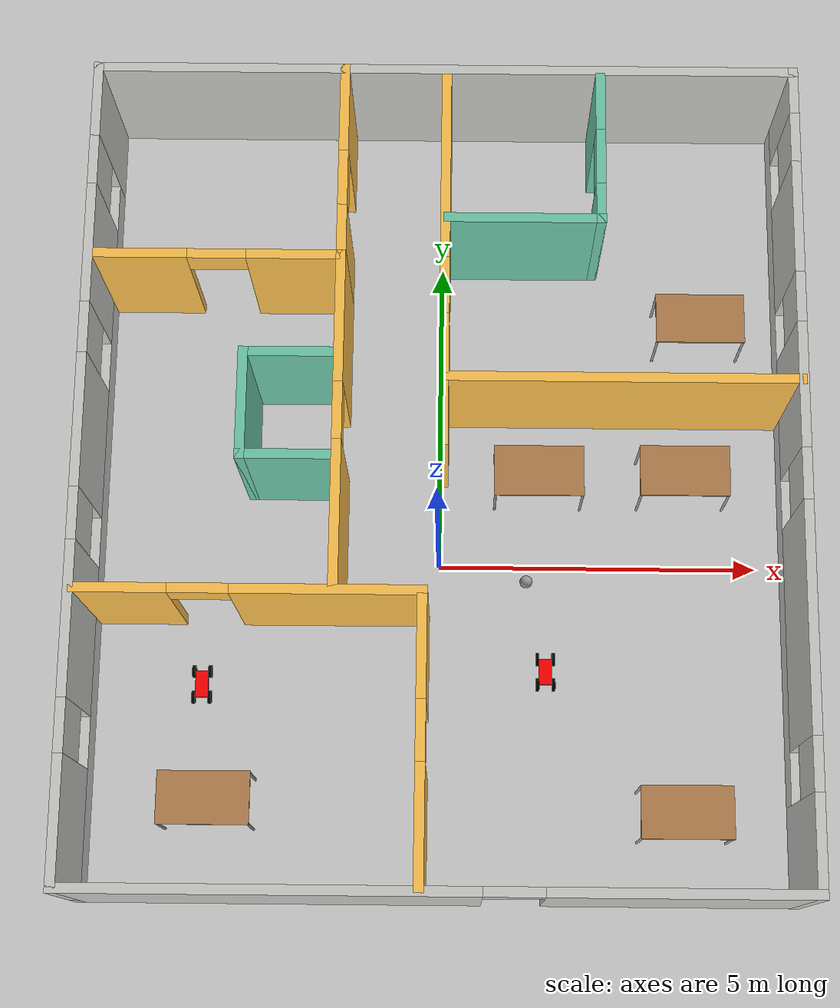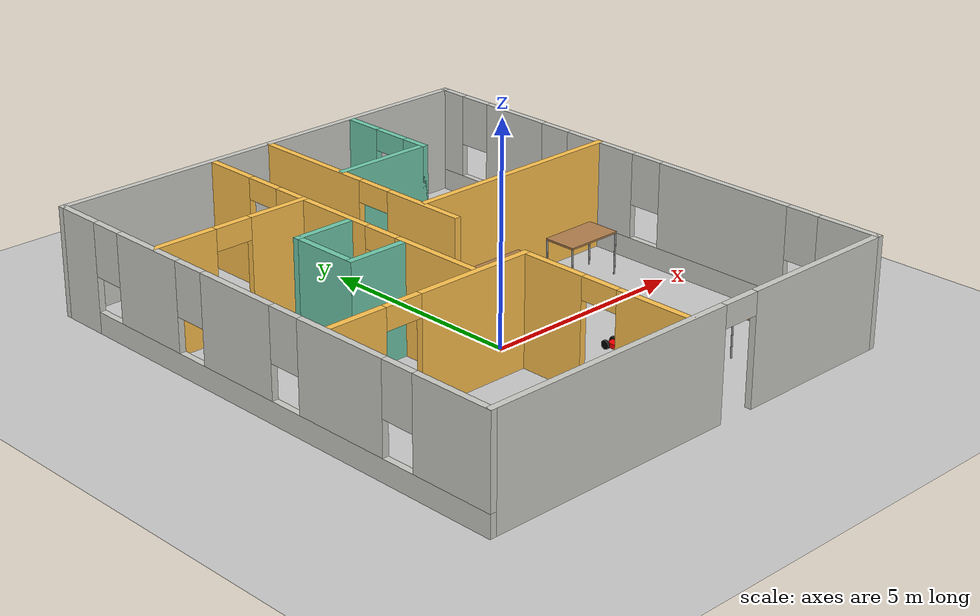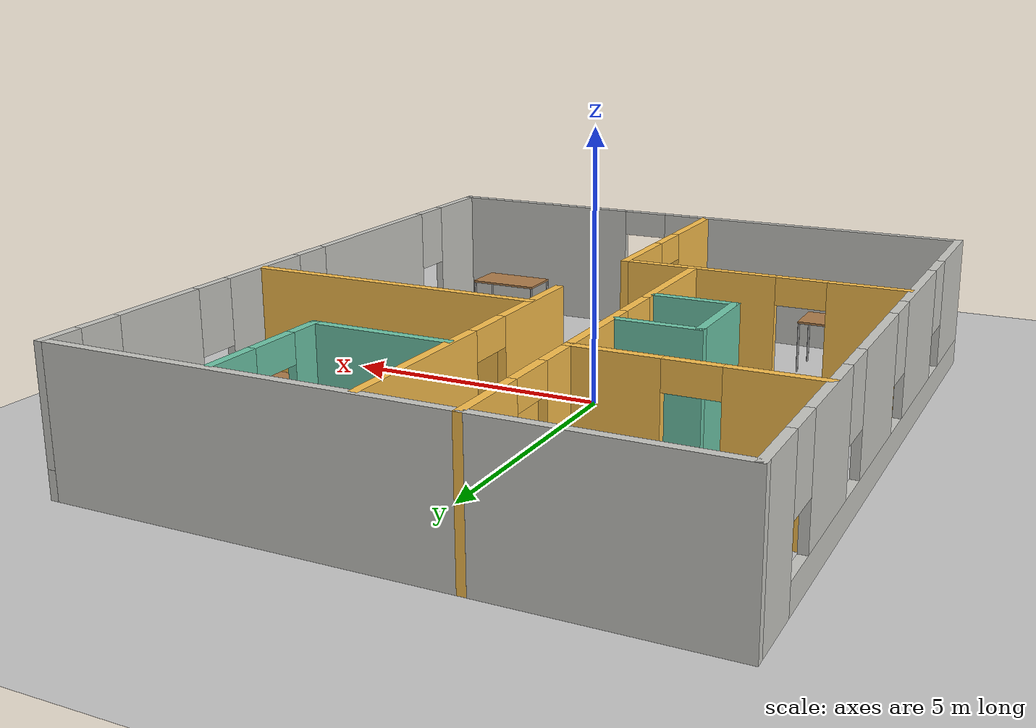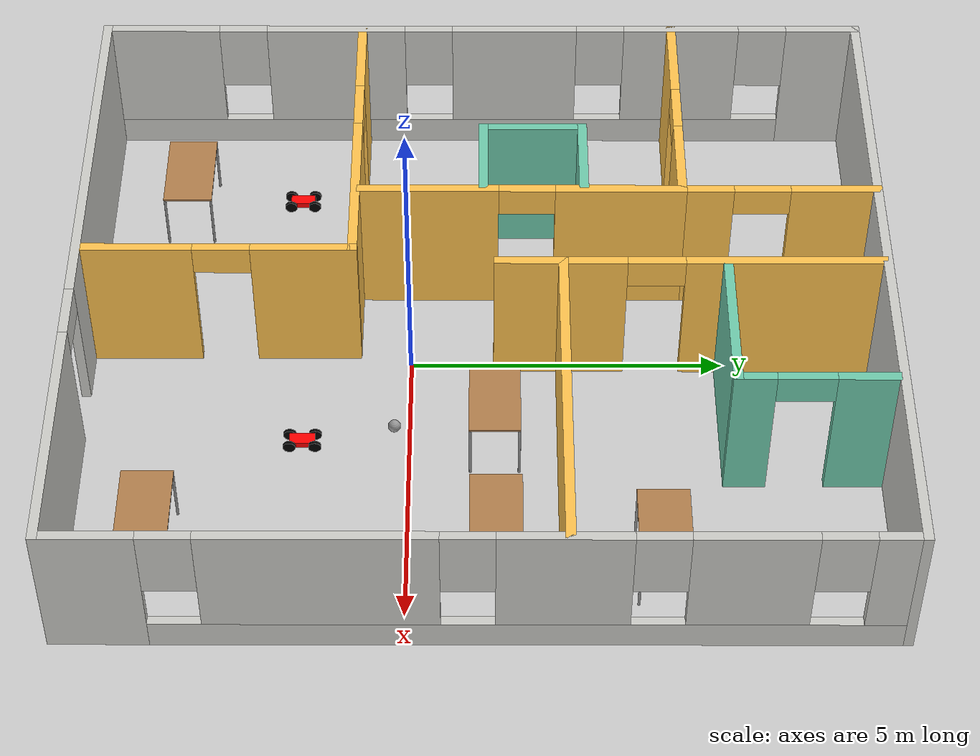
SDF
<sdf version="1.6">
 <world name="default">
  <plugin name="welcome" filename="libwelcome.so"/>
  <light name="sun" type="directional">
   <pose>0 0 10 0 -0 0</pose>
   <diffuse>0.8 0.8 0.8 1</diffuse>
   <specular>0.1 0.1 0.1 1</specular>
   <attenuation>
    <range>1000</range>
    <constant>0.9</constant>
    <linear>0.01</linear>
    <quadratic>0.001</quadratic>
   </attenuation>
   <direction>-0.5 0.5 -1</direction>
  </light>
  <model name="ground_plane">
   <static>1</static>
   <link name="link">
    <collision name="collision">
     <geometry><plane><normal>0 0 1</normal><size>100 100</size></plane></geometry>
     <surface><friction><ode><mu>100</mu><mu2>50</mu2></ode></friction></surface>
    </collision>
    <visual name="visual">
     <cast_shadows>0</cast_shadows>
     <geometry><plane><normal>0 0 1</normal><size>100 100</size></plane></geometry>
     <material>
      <script><uri>file://media/materials/scripts/gazebo.material</uri><name>Gazebo/Grey</name></script>
     </material>
    </visual>
   </link>
  </model>
  <gravity>0 0 -9.8</gravity>
  <magnetic_field>6e-06 2.3e-05 -4.2e-05</magnetic_field>
  <atmosphere type="adiabatic"/>
  <physics name="default_physics" default="0" type="ode">
   <max_step_size>0.001</max_step_size>
   <real_time_factor>1</real_time_factor>
   <real_time_update_rate>1000</real_time_update_rate>
  </physics>
  <scene><ambient>0.4 0.4 0.4 1</ambient><background>0.7 0.7 0.7 1</background><shadows>1</shadows></scene>
  <spherical_coordinates>
   <surface_model>EARTH_WGS84</surface_model>
   <latitude_deg>0</latitude_deg>
   <longitude_deg>0</longitude_deg>
   <elevation>0</elevation>
   <heading_deg>0</heading_deg>
  </spherical_coordinates>
  <model name="my_building">
   <pose>0.030865 1.12129 0 0 -0 0</pose>
   <link name="Wall_16">
    <pose>0 -6.30017 0 0 -0 0</pose>
    <visual name="Wall_16_Visual_0">
     <pose>-2.42617 0 1.25 0 -0 0</pose>
     <geometry><box><size>6.14766 0.15 2.5</size></box></geometry>
     <material>
      <script><uri>file://media/materials/scripts/gazebo.material</uri><name>Gazebo/CeilingTiled</name></script>
      <ambient>1 1 1 1</ambient>
     </material>
    </visual>
    <collision name="Wall_16_Collision_0">
     <geometry><box><size>6.14766 0.15 2.5</size></box></geometry>
     <pose>-2.42617 0 1.25 0 -0 0</pose>
    </collision>
    <visual name="Wall_16_Visual_1">
     <pose>3.52383 0 1.25 0 -0 0</pose>
     <geometry><box><size>3.95234 0.15 2.5</size></box></geometry>
     <material>
      <script><uri>file://media/materials/scripts/gazebo.material</uri><name>Gazebo/CeilingTiled</name></script>
      <ambient>1 1 1 1</ambient>
     </material>
    </visual>
    <collision name="Wall_16_Collision_1">
     <geometry><box><size>3.95234 0.15 2.5</size></box></geometry>
     <pose>3.52383 0 1.25 0 -0 0</pose>
    </collision>
    <visual name="Wall_16_Visual_2">
     <pose>1.09766 0 2.25 0 -0 0</pose>
     <geometry><box><size>0.9 0.15 0.5</size></box></geometry>
     <material>
      <script><uri>file://media/materials/scripts/gazebo.material</uri><name>Gazebo/CeilingTiled</name></script>
      <ambient>1 1 1 1</ambient>
     </material>
    </visual>
    <collision name="Wall_16_Collision_2">
     <geometry><box><size>0.9 0.15 0.5</size></box></geometry>
     <pose>1.09766 0 2.25 0 -0 0</pose>
    </collision>
   </link>
   <link name="Wall_17">
    <pose>5.425 -0.000173 0 0 -0 1.5708</pose>
    <visual name="Wall_17_Visual_0">
     <pose>-5.62049 0 1.25 0 -0 0</pose>
     <geometry><box><size>1.50902 0.15 2.5</size></box></geometry>
     <material>
      <script><uri>file://media/materials/scripts/gazebo.material</uri><name>Gazebo/CeilingTiled</name></script>
      <ambient>1 1 1 1</ambient>
     </material>
    </visual>
    <collision name="Wall_17_Collision_0">
     <geometry><box><size>1.50902 0.15 2.5</size></box></geometry>
     <pose>-5.62049 0 1.25 0 -0 0</pose>
    </collision>
    <visual name="Wall_17_Visual_1">
     <pose>0.754508 0 0.25 0 -0 0</pose>
     <geometry><box><size>11.241 0.15 0.5</size></box></geometry>
     <material>
      <script><uri>file://media/materials/scripts/gazebo.material</uri><name>Gazebo/CeilingTiled</name></script>
      <ambient>1 1 1 1</ambient>
     </material>
    </visual>
    <collision name="Wall_17_Collision_1">
     <geometry><box><size>11.241 0.15 0.5</size></box></geometry>
     <pose>0.754508 0 0.25 0 -0 0</pose>
    </collision>
    <visual name="Wall_17_Visual_2">
     <pose>-2.32184 0 1.5 0 -0 0</pose>
     <geometry><box><size>3.48829 0.15 2</size></box></geometry>
     <material>
      <script><uri>file://media/materials/scripts/gazebo.material</uri><name>Gazebo/CeilingTiled</name></script>
      <ambient>1 1 1 1</ambient>
     </material>
    </visual>
    <collision name="Wall_17_Collision_2">
     <geometry><box><size>3.48829 0.15 2</size></box></geometry>
     <pose>-2.32184 0 1.5 0 -0 0</pose>
    </collision>
    <visual name="Wall_17_Visual_3">
     <pose>1.20791 0 1.5 0 -0 0</pose>
     <geometry><box><size>1.97121 0.15 2</size></box></geometry>
     <material>
      <script><uri>file://media/materials/scripts/gazebo.material</uri><name>Gazebo/CeilingTiled</name></script>
      <ambient>1 1 1 1</ambient>
     </material>
    </visual>
    <collision name="Wall_17_Collision_3">
     <geometry><box><size>1.97121 0.15 2</size></box></geometry>
     <pose>1.20791 0 1.5 0 -0 0</pose>
    </collision>
    <visual name="Wall_17_Visual_4">
     <pose>3.89821 0 1.5 0 -0 0</pose>
     <geometry><box><size>1.80939 0.15 2</size></box></geometry>
     <material>
      <script><uri>file://media/materials/scripts/gazebo.material</uri><name>Gazebo/CeilingTiled</name></script>
      <ambient>1 1 1 1</ambient>
     </material>
    </visual>
    <collision name="Wall_17_Collision_4">
     <geometry><box><size>1.80939 0.15 2</size></box></geometry>
     <pose>3.89821 0 1.5 0 -0 0</pose>
    </collision>
    <visual name="Wall_17_Visual_5">
     <pose>5.98895 0 1.5 0 -0 0</pose>
     <geometry><box><size>0.772101 0.15 2</size></box></geometry>
     <material>
      <script><uri>file://media/materials/scripts/gazebo.material</uri><name>Gazebo/CeilingTiled</name></script>
      <ambient>1 1 1 1</ambient>
     </material>
    </visual>
    <collision name="Wall_17_Collision_5">
     <geometry><box><size>0.772101 0.15 2</size></box></geometry>
     <pose>5.98895 0 1.5 0 -0 0</pose>
    </collision>
    <visual name="Wall_17_Visual_6">
     <pose>-4.46598 0 1.9 0 -0 0</pose>
     <geometry><box><size>0.8 0.15 1.2</size></box></geometry>
     <material>
      <script><uri>file://media/materials/scripts/gazebo.material</uri><name>Gazebo/CeilingTiled</name></script>
      <ambient>1 1 1 1</ambient>
     </material>
    </visual>
    <collision name="Wall_17_Collision_6">
     <geometry><box><size>0.8 0.15 1.2</size></box></geometry>
     <pose>-4.46598 0 1.9 0 -0 0</pose>
    </collision>
    <visual name="Wall_17_Visual_7">
     <pose>-0.177693 0 1.9 0 -0 0</pose>
     <geometry><box><size>0.8 0.15 1.2</size></box></geometry>
     <material>
      <script><uri>file://media/materials/scripts/gazebo.material</uri><name>Gazebo/CeilingTiled</name></script>
      <ambient>1 1 1 1</ambient>
     </material>
    </visual>
    <collision name="Wall_17_Collision_7">
     <geometry><box><size>0.8 0.15 1.2</size></box></geometry>
     <pose>-0.177693 0 1.9 0 -0 0</pose>
    </collision>
    <visual name="Wall_17_Visual_8">
     <pose>2.59351 0 1.9 0 -0 0</pose>
     <geometry><box><size>0.8 0.15 1.2</size></box></geometry>
     <material>
      <script><uri>file://media/materials/scripts/gazebo.material</uri><name>Gazebo/CeilingTiled</name></script>
      <ambient>1 1 1 1</ambient>
     </material>
    </visual>
    <collision name="Wall_17_Collision_8">
     <geometry><box><size>0.8 0.15 1.2</size></box></geometry>
     <pose>2.59351 0 1.9 0 -0 0</pose>
    </collision>
    <visual name="Wall_17_Visual_9">
     <pose>5.2029 0 1.9 0 -0 0</pose>
     <geometry><box><size>0.8 0.15 1.2</size></box></geometry>
     <material>
      <script><uri>file://media/materials/scripts/gazebo.material</uri><name>Gazebo/CeilingTiled</name></script>
      <ambient>1 1 1 1</ambient>
     </material>
    </visual>
    <collision name="Wall_17_Collision_9">
     <geometry><box><size>0.8 0.15 1.2</size></box></geometry>
     <pose>5.2029 0 1.9 0 -0 0</pose>
    </collision>
   </link>
   <link name="Wall_19">
    <collision name="Wall_19_Collision">
     <geometry><box><size>11 0.15 2.5</size></box></geometry>
     <pose>0 0 1.25 0 -0 0</pose>
    </collision>
    <visual name="Wall_19_Visual">
     <pose>0 0 1.25 0 -0 0</pose>
     <geometry><box><size>11 0.15 2.5</size></box></geometry>
     <material>
      <script><uri>file://media/materials/scripts/gazebo.material</uri><name>Gazebo/CeilingTiled</name></script>
      <ambient>1 1 1 1</ambient>
     </material>
    </visual>
    <pose>0 6.29983 0 0 -0 3.14159</pose>
   </link>
   <link name="Wall_20">
    <pose>-5.425 -0.000173 0 0 0 -1.5708</pose>
    <visual name="Wall_20_Visual_0">
     <pose>-5.75633 0 1.25 0 -0 0</pose>
     <geometry><box><size>1.23734 0.15 2.5</size></box></geometry>
     <material>
      <script><uri>file://media/materials/scripts/gazebo.material</uri><name>Gazebo/CeilingTiled</name></script>
      <ambient>1 1 1 1</ambient>
     </material>
    </visual>
    <collision name="Wall_20_Collision_0">
     <geometry><box><size>1.23734 0.15 2.5</size></box></geometry>
     <pose>-5.75633 0 1.25 0 -0 0</pose>
    </collision>
    <visual name="Wall_20_Visual_1">
     <pose>0.61867 0 0.25 0 -0 0</pose>
     <geometry><box><size>11.5127 0.15 0.5</size></box></geometry>
     <material>
      <script><uri>file://media/materials/scripts/gazebo.material</uri><name>Gazebo/CeilingTiled</name></script>
      <ambient>1 1 1 1</ambient>
     </material>
    </visual>
    <collision name="Wall_20_Collision_1">
     <geometry><box><size>11.5127 0.15 0.5</size></box></geometry>
     <pose>0.61867 0 0.25 0 -0 0</pose>
    </collision>
    <visual name="Wall_20_Visual_2">
     <pose>-3.37228 0 1.5 0 -0 0</pose>
     <geometry><box><size>1.93075 0.15 2</size></box></geometry>
     <material>
      <script><uri>file://media/materials/scripts/gazebo.material</uri><name>Gazebo/CeilingTiled</name></script>
      <ambient>1 1 1 1</ambient>
     </material>
    </visual>
    <collision name="Wall_20_Collision_2">
     <geometry><box><size>1.93075 0.15 2</size></box></geometry>
     <pose>-3.37228 0 1.5 0 -0 0</pose>
    </collision>
    <visual name="Wall_20_Visual_3">
     <pose>-0.560621 0 1.5 0 -0 0</pose>
     <geometry><box><size>2.09257 0.15 2</size></box></geometry>
     <material>
      <script><uri>file://media/materials/scripts/gazebo.material</uri><name>Gazebo/CeilingTiled</name></script>
      <ambient>1 1 1 1</ambient>
     </material>
    </visual>
    <collision name="Wall_20_Collision_3">
     <geometry><box><size>2.09257 0.15 2</size></box></geometry>
     <pose>-0.560621 0 1.5 0 -0 0</pose>
    </collision>
    <visual name="Wall_20_Visual_4">
     <pose>2.45016 0 1.5 0 -0 0</pose>
     <geometry><box><size>2.32899 0.15 2</size></box></geometry>
     <material>
      <script><uri>file://media/materials/scripts/gazebo.material</uri><name>Gazebo/CeilingTiled</name></script>
      <ambient>1 1 1 1</ambient>
     </material>
    </visual>
    <collision name="Wall_20_Collision_4">
     <geometry><box><size>2.32899 0.15 2</size></box></geometry>
     <pose>2.45016 0 1.5 0 -0 0</pose>
    </collision>
    <visual name="Wall_20_Visual_5">
     <pose>5.39483 0 1.5 0 -0 0</pose>
     <geometry><box><size>1.96034 0.15 2</size></box></geometry>
     <material>
      <script><uri>file://media/materials/scripts/gazebo.material</uri><name>Gazebo/CeilingTiled</name></script>
      <ambient>1 1 1 1</ambient>
     </material>
    </visual>
    <collision name="Wall_20_Collision_5">
     <geometry><box><size>1.96034 0.15 2</size></box></geometry>
     <pose>5.39483 0 1.5 0 -0 0</pose>
    </collision>
    <visual name="Wall_20_Visual_6">
     <pose>-4.73766 0 1.9 0 -0 0</pose>
     <geometry><box><size>0.8 0.15 1.2</size></box></geometry>
     <material>
      <script><uri>file://media/materials/scripts/gazebo.material</uri><name>Gazebo/CeilingTiled</name></script>
      <ambient>1 1 1 1</ambient>
     </material>
    </visual>
    <collision name="Wall_20_Collision_6">
     <geometry><box><size>0.8 0.15 1.2</size></box></geometry>
     <pose>-4.73766 0 1.9 0 -0 0</pose>
    </collision>
    <visual name="Wall_20_Visual_7">
     <pose>-2.00691 0 1.9 0 -0 0</pose>
     <geometry><box><size>0.8 0.15 1.2</size></box></geometry>
     <material>
      <script><uri>file://media/materials/scripts/gazebo.material</uri><name>Gazebo/CeilingTiled</name></script>
      <ambient>1 1 1 1</ambient>
     </material>
    </visual>
    <collision name="Wall_20_Collision_7">
     <geometry><box><size>0.8 0.15 1.2</size></box></geometry>
     <pose>-2.00691 0 1.9 0 -0 0</pose>
    </collision>
    <visual name="Wall_20_Visual_8">
     <pose>0.885666 0 1.9 0 -0 0</pose>
     <geometry><box><size>0.8 0.15 1.2</size></box></geometry>
     <material>
      <script><uri>file://media/materials/scripts/gazebo.material</uri><name>Gazebo/CeilingTiled</name></script>
      <ambient>1 1 1 1</ambient>
     </material>
    </visual>
    <collision name="Wall_20_Collision_8">
     <geometry><box><size>0.8 0.15 1.2</size></box></geometry>
     <pose>0.885666 0 1.9 0 -0 0</pose>
    </collision>
    <visual name="Wall_20_Visual_9">
     <pose>4.01466 0 1.9 0 -0 0</pose>
     <geometry><box><size>0.8 0.15 1.2</size></box></geometry>
     <material>
      <script><uri>file://media/materials/scripts/gazebo.material</uri><name>Gazebo/CeilingTiled</name></script>
      <ambient>1 1 1 1</ambient>
     </material>
    </visual>
    <collision name="Wall_20_Collision_9">
     <geometry><box><size>0.8 0.15 1.2</size></box></geometry>
     <pose>4.01466 0 1.9 0 -0 0</pose>
    </collision>
   </link>
   <link name="Wall_22">
    <pose>-2.805 -1.99837 0 0 -0 0</pose>
    <visual name="Wall_22_Visual_0">
     <pose>-1.90225 0 1.25 0 -0 0</pose>
     <geometry><box><size>1.4455 0.15 2.5</size></box></geometry>
     <material>
      <script><uri>file://media/materials/scripts/gazebo.material</uri><name>Gazebo/Grey</name></script>
      <ambient>1 0.764706 0.305882 1</ambient>
     </material>
    </visual>
    <collision name="Wall_22_Collision_0">
     <geometry><box><size>1.4455 0.15 2.5</size></box></geometry>
     <pose>-1.90225 0 1.25 0 -0 0</pose>
    </collision>
    <visual name="Wall_22_Visual_1">
     <pose>1.17275 0 1.25 0 -0 0</pose>
     <geometry><box><size>2.9045 0.15 2.5</size></box></geometry>
     <material>
      <script><uri>file://media/materials/scripts/gazebo.material</uri><name>Gazebo/Grey</name></script>
      <ambient>1 0.764706 0.305882 1</ambient>
     </material>
    </visual>
    <collision name="Wall_22_Collision_1">
     <geometry><box><size>2.9045 0.15 2.5</size></box></geometry>
     <pose>1.17275 0 1.25 0 -0 0</pose>
    </collision>
    <visual name="Wall_22_Visual_2">
     <pose>-0.729499 0 2.25 0 -0 0</pose>
     <geometry><box><size>0.9 0.15 0.5</size></box></geometry>
     <material>
      <script><uri>file://media/materials/scripts/gazebo.material</uri><name>Gazebo/Grey</name></script>
      <ambient>1 0.764706 0.305882 1</ambient>
     </material>
    </visual>
    <collision name="Wall_22_Collision_2">
     <geometry><box><size>0.9 0.15 0.5</size></box></geometry>
     <pose>-0.729499 0 2.25 0 -0 0</pose>
    </collision>
   </link>
   <link name="Wall_23">
    <pose>-0.255 -4.12337 0 0 0 -1.5708</pose>
    <visual name="Wall_23_Visual_0">
     <pose>-1.366 0 1.25 0 -0 0</pose>
     <geometry><box><size>1.66801 0.15 2.5</size></box></geometry>
     <material>
      <script><uri>file://media/materials/scripts/gazebo.material</uri><name>Gazebo/Grey</name></script>
      <ambient>1 0.764706 0.305882 1</ambient>
     </material>
    </visual>
    <collision name="Wall_23_Collision_0">
     <geometry><box><size>1.66801 0.15 2.5</size></box></geometry>
     <pose>-1.366 0 1.25 0 -0 0</pose>
    </collision>
    <visual name="Wall_23_Visual_1">
     <pose>1.284 0 1.25 0 -0 0</pose>
     <geometry><box><size>1.83199 0.15 2.5</size></box></geometry>
     <material>
      <script><uri>file://media/materials/scripts/gazebo.material</uri><name>Gazebo/Grey</name></script>
      <ambient>1 0.764706 0.305882 1</ambient>
     </material>
    </visual>
    <collision name="Wall_23_Collision_1">
     <geometry><box><size>1.83199 0.15 2.5</size></box></geometry>
     <pose>1.284 0 1.25 0 -0 0</pose>
    </collision>
    <visual name="Wall_23_Visual_2">
     <pose>-0.081993 0 2.25 0 -0 0</pose>
     <geometry><box><size>0.9 0.15 0.5</size></box></geometry>
     <material>
      <script><uri>file://media/materials/scripts/gazebo.material</uri><name>Gazebo/Grey</name></script>
      <ambient>1 0.764706 0.305882 1</ambient>
     </material>
    </visual>
    <collision name="Wall_23_Collision_2">
     <geometry><box><size>0.9 0.15 0.5</size></box></geometry>
     <pose>-0.081993 0 2.25 0 -0 0</pose>
    </collision>
   </link>
   <link name="Wall_25">
    <pose>-3.49068 3.20017 0 0 -0 0</pose>
    <visual name="Wall_25_Visual_0">
     <pose>-1.21338 0 1.25 0 -0 0</pose>
     <geometry><box><size>1.57325 0.15 2.5</size></box></geometry>
     <material>
      <script><uri>file://media/materials/scripts/gazebo.material</uri><name>Gazebo/Grey</name></script>
      <ambient>1 0.764706 0.305882 1</ambient>
     </material>
    </visual>
    <collision name="Wall_25_Collision_0">
     <geometry><box><size>1.57325 0.15 2.5</size></box></geometry>
     <pose>-1.21338 0 1.25 0 -0 0</pose>
    </collision>
    <visual name="Wall_25_Visual_1">
     <pose>1.23662 0 1.25 0 -0 0</pose>
     <geometry><box><size>1.52675 0.15 2.5</size></box></geometry>
     <material>
      <script><uri>file://media/materials/scripts/gazebo.material</uri><name>Gazebo/Grey</name></script>
      <ambient>1 0.764706 0.305882 1</ambient>
     </material>
    </visual>
    <collision name="Wall_25_Collision_1">
     <geometry><box><size>1.52675 0.15 2.5</size></box></geometry>
     <pose>1.23662 0 1.25 0 -0 0</pose>
    </collision>
    <visual name="Wall_25_Visual_2">
     <pose>0.023247 0 2.25 0 -0 0</pose>
     <geometry><box><size>0.9 0.15 0.5</size></box></geometry>
     <material>
      <script><uri>file://media/materials/scripts/gazebo.material</uri><name>Gazebo/Grey</name></script>
      <ambient>1 0.764706 0.305882 1</ambient>
     </material>
    </visual>
    <collision name="Wall_25_Collision_2">
     <geometry><box><size>0.9 0.15 0.5</size></box></geometry>
     <pose>0.023247 0 2.25 0 -0 0</pose>
    </collision>
   </link>
   <link name="Wall_26">
    <pose>-1.56568 0.650174 0 0 0 -1.5708</pose>
    <visual name="Wall_26_Visual_0">
     <pose>-1.57861 0 1.25 0 -0 0</pose>
     <geometry><box><size>2.09279 0.15 2.5</size></box></geometry>
     <material>
      <script><uri>file://media/materials/scripts/gazebo.material</uri><name>Gazebo/Grey</name></script>
      <ambient>1 0.764706 0.305882 1</ambient>
     </material>
    </visual>
    <collision name="Wall_26_Collision_0">
     <geometry><box><size>2.09279 0.15 2.5</size></box></geometry>
     <pose>-1.57861 0 1.25 0 -0 0</pose>
    </collision>
    <visual name="Wall_26_Visual_1">
     <pose>1.49639 0 1.25 0 -0 0</pose>
     <geometry><box><size>2.25721 0.15 2.5</size></box></geometry>
     <material>
      <script><uri>file://media/materials/scripts/gazebo.material</uri><name>Gazebo/Grey</name></script>
      <ambient>1 0.764706 0.305882 1</ambient>
     </material>
    </visual>
    <collision name="Wall_26_Collision_1">
     <geometry><box><size>2.25721 0.15 2.5</size></box></geometry>
     <pose>1.49639 0 1.25 0 -0 0</pose>
    </collision>
    <visual name="Wall_26_Visual_2">
     <pose>-0.08221 0 2.25 0 -0 0</pose>
     <geometry><box><size>0.9 0.15 0.5</size></box></geometry>
     <material>
      <script><uri>file://media/materials/scripts/gazebo.material</uri><name>Gazebo/Grey</name></script>
      <ambient>1 0.764706 0.305882 1</ambient>
     </material>
    </visual>
    <collision name="Wall_26_Collision_2">
     <geometry><box><size>0.9 0.15 0.5</size></box></geometry>
     <pose>-0.08221 0 2.25 0 -0 0</pose>
    </collision>
   </link>
   <link name="Wall_28">
    <pose>-1.56568 4.75017 0 0 -0 1.5708</pose>
    <visual name="Wall_28_Visual_0">
     <pose>-1.17532 0 1.25 0 -0 0</pose>
     <geometry><box><size>0.89935 0.15 2.5</size></box></geometry>
     <material>
      <script><uri>file://media/materials/scripts/gazebo.material</uri><name>Gazebo/Grey</name></script>
      <ambient>1 0.764706 0.305882 1</ambient>
     </material>
    </visual>
    <collision name="Wall_28_Collision_0">
     <geometry><box><size>0.89935 0.15 2.5</size></box></geometry>
     <pose>-1.17532 0 1.25 0 -0 0</pose>
    </collision>
    <visual name="Wall_28_Visual_1">
     <pose>0.899675 0 1.25 0 -0 0</pose>
     <geometry><box><size>1.45065 0.15 2.5</size></box></geometry>
     <material>
      <script><uri>file://media/materials/scripts/gazebo.material</uri><name>Gazebo/Grey</name></script>
      <ambient>1 0.764706 0.305882 1</ambient>
     </material>
    </visual>
    <collision name="Wall_28_Collision_1">
     <geometry><box><size>1.45065 0.15 2.5</size></box></geometry>
     <pose>0.899675 0 1.25 0 -0 0</pose>
    </collision>
    <visual name="Wall_28_Visual_2">
     <pose>-0.27565 0 2.25 0 -0 0</pose>
     <geometry><box><size>0.9 0.15 0.5</size></box></geometry>
     <material>
      <script><uri>file://media/materials/scripts/gazebo.material</uri><name>Gazebo/Grey</name></script>
      <ambient>1 0.764706 0.305882 1</ambient>
     </material>
    </visual>
    <collision name="Wall_28_Collision_2">
     <geometry><box><size>0.9 0.15 0.5</size></box></geometry>
     <pose>-0.27565 0 2.25 0 -0 0</pose>
    </collision>
   </link>
   <link name="Wall_30">
    <collision name="Wall_30_Collision">
     <geometry><box><size>1.5 0.15 2.5</size></box></geometry>
     <pose>0 0 1.25 0 -0 0</pose>
    </collision>
    <visual name="Wall_30_Visual">
     <pose>0 0 1.25 0 -0 0</pose>
     <geometry><box><size>1.5 0.15 2.5</size></box></geometry>
     <material>
      <script><uri>file://media/materials/scripts/gazebo.material</uri><name>Gazebo/Grey</name></script>
      <ambient>0.435294 0.796078 0.67451 1</ambient>
     </material>
    </visual>
    <pose>-2.32831 1.64264 0 0 -0 3.14159</pose>
   </link>
   <link name="Wall_31">
    <collision name="Wall_31_Collision">
     <geometry><box><size>1.75 0.15 2.5</size></box></geometry>
     <pose>0 0 1.25 0 -0 0</pose>
    </collision>
    <visual name="Wall_31_Visual">
     <pose>0 0 1.25 0 -0 0</pose>
     <geometry><box><size>1.75 0.15 2.5</size></box></geometry>
     <material>
      <script><uri>file://media/materials/scripts/gazebo.material</uri><name>Gazebo/Grey</name></script>
      <ambient>0.435294 0.796078 0.67451 1</ambient>
     </material>
    </visual>
    <pose>-3.00331 0.842635 0 0 0 -1.5708</pose>
   </link>
   <link name="Wall_32">
    <collision name="Wall_32_Collision">
     <geometry><box><size>1.5 0.15 2.5</size></box></geometry>
     <pose>0 0 1.25 0 -0 0</pose>
    </collision>
    <visual name="Wall_32_Visual">
     <pose>0 0 1.25 0 -0 0</pose>
     <geometry><box><size>1.5 0.15 2.5</size></box></geometry>
     <material>
      <script><uri>file://media/materials/scripts/gazebo.material</uri><name>Gazebo/Grey</name></script>
      <ambient>0.435294 0.796078 0.67451 1</ambient>
     </material>
    </visual>
    <pose>-2.32831 0.042635 0 0 -0 0</pose>
   </link>
   <link name="Wall_37">
    <collision name="Wall_37_Collision">
     <geometry><box><size>5.5 0.15 2.5</size></box></geometry>
     <pose>0 0 1.25 0 -0 0</pose>
    </collision>
    <visual name="Wall_37_Visual">
     <pose>0 0 1.25 0 -0 0</pose>
     <geometry><box><size>5.5 0.15 2.5</size></box></geometry>
     <material>
      <script><uri>file://media/materials/scripts/gazebo.material</uri><name>Gazebo/Grey</name></script>
      <ambient>1 0.764706 0.305882 1</ambient>
     </material>
    </visual>
    <pose>2.72082 1.27853 0 0 -0 0</pose>
   </link>
   <link name="Wall_39">
    <collision name="Wall_39_Collision">
     <geometry><box><size>2.5 0.15 2.5</size></box></geometry>
     <pose>0 0 1.25 0 -0 0</pose>
    </collision>
    <visual name="Wall_39_Visual">
     <pose>0 0 1.25 0 -0 0</pose>
     <geometry><box><size>2.5 0.15 2.5</size></box></geometry>
     <material>
      <script><uri>file://media/materials/scripts/gazebo.material</uri><name>Gazebo/Grey</name></script>
      <ambient>0.435294 0.796078 0.67451 1</ambient>
     </material>
    </visual>
    <pose>1.24105 3.82724 0 0 -0 0</pose>
   </link>
   <link name="Wall_40">
    <pose>2.41605 5.00224 0 0 -0 1.5708</pose>
    <visual name="Wall_40_Visual_0">
     <pose>-0.921692 0 1.25 0 -0 0</pose>
     <geometry><box><size>0.656617 0.15 2.5</size></box></geometry>
     <material>
      <script><uri>file://media/materials/scripts/gazebo.material</uri><name>Gazebo/Grey</name></script>
      <ambient>0.435294 0.796078 0.67451 1</ambient>
     </material>
    </visual>
    <collision name="Wall_40_Collision_0">
     <geometry><box><size>0.656617 0.15 2.5</size></box></geometry>
     <pose>-0.921692 0 1.25 0 -0 0</pose>
    </collision>
    <visual name="Wall_40_Visual_1">
     <pose>0.778308 0 1.25 0 -0 0</pose>
     <geometry><box><size>0.943383 0.15 2.5</size></box></geometry>
     <material>
      <script><uri>file://media/materials/scripts/gazebo.material</uri><name>Gazebo/Grey</name></script>
      <ambient>0.435294 0.796078 0.67451 1</ambient>
     </material>
    </visual>
    <collision name="Wall_40_Collision_1">
     <geometry><box><size>0.943383 0.15 2.5</size></box></geometry>
     <pose>0.778308 0 1.25 0 -0 0</pose>
    </collision>
    <visual name="Wall_40_Visual_2">
     <pose>-0.143383 0 2.25 0 -0 0</pose>
     <geometry><box><size>0.9 0.15 0.5</size></box></geometry>
     <material>
      <script><uri>file://media/materials/scripts/gazebo.material</uri><name>Gazebo/Grey</name></script>
      <ambient>0.435294 0.796078 0.67451 1</ambient>
     </material>
    </visual>
    <collision name="Wall_40_Collision_2">
     <geometry><box><size>0.9 0.15 0.5</size></box></geometry>
     <pose>-0.143383 0 2.25 0 -0 0</pose>
    </collision>
   </link>
   <link name="Wall_42">
    <pose>0.021649 3.25468 0 0 -0 1.5708</pose>
    <visual name="Wall_42_Visual_0">
     <pose>-2.01275 0 1.25 0 -0 0</pose>
     <geometry><box><size>2.0745 0.15 2.5</size></box></geometry>
     <material>
      <script><uri>file://media/materials/scripts/gazebo.material</uri><name>Gazebo/Grey</name></script>
      <ambient>1 0.764706 0.305882 1</ambient>
     </material>
    </visual>
    <collision name="Wall_42_Collision_0">
     <geometry><box><size>2.0745 0.15 2.5</size></box></geometry>
     <pose>-2.01275 0 1.25 0 -0 0</pose>
    </collision>
    <visual name="Wall_42_Visual_1">
     <pose>1.48725 0 1.25 0 -0 0</pose>
     <geometry><box><size>3.1255 0.15 2.5</size></box></geometry>
     <material>
      <script><uri>file://media/materials/scripts/gazebo.material</uri><name>Gazebo/Grey</name></script>
      <ambient>1 0.764706 0.305882 1</ambient>
     </material>
    </visual>
    <collision name="Wall_42_Collision_1">
     <geometry><box><size>3.1255 0.15 2.5</size></box></geometry>
     <pose>1.48725 0 1.25 0 -0 0</pose>
    </collision>
    <visual name="Wall_42_Visual_2">
     <pose>-0.5255 0 2.25 0 -0 0</pose>
     <geometry><box><size>0.9 0.15 0.5</size></box></geometry>
     <material>
      <script><uri>file://media/materials/scripts/gazebo.material</uri><name>Gazebo/Grey</name></script>
      <ambient>1 0.764706 0.305882 1</ambient>
     </material>
    </visual>
    <collision name="Wall_42_Collision_2">
     <geometry><box><size>0.9 0.15 0.5</size></box></geometry>
     <pose>-0.5255 0 2.25 0 -0 0</pose>
    </collision>
   </link>
   <static>1</static>
  </model>
  <model name="my_robot">
   <link name="link_0">
    <inertial>
     <mass>1</mass>
     <inertia>
      <ixx>0.166667</ixx>
      <ixy>0</ixy>
      <ixz>0</ixz>
      <iyy>0.166667</iyy>
      <iyz>0</iyz>
      <izz>0.166667</izz>
     </inertia>
    </inertial>
    <visual name="visual">
     <geometry><box><size>0.4 0.2 0.1</size></box></geometry>
     <material>
      <ambient>1 0 0 1</ambient>
      <diffuse>1 0 0 1</diffuse>
      <specular>0.1 0.1 0.1 1</specular>
      <emissive>0 0 0 0</emissive>
     </material>
    </visual>
    <collision name="collision">
     <geometry><box><size>0.4 0.2 0.1</size></box></geometry>
     <surface>
      <friction>
       <ode><mu>1</mu><mu2>1</mu2><fdir1>0 0 0</fdir1><slip1>0</slip1><slip2>0</slip2></ode>
       <torsional>
        <coefficient>1</coefficient>
        <patch_radius>0</patch_radius>
        <surface_radius>0</surface_radius>
        <use_patch_radius>1</use_patch_radius>
        <ode><slip>0</slip></ode>
       </torsional>
      </friction>
      <bounce><restitution_coefficient>0</restitution_coefficient><threshold>1e+06</threshold></bounce>
      <contact>
       <collide_without_contact>0</collide_without_contact>
       <collide_without_contact_bitmask>1</collide_without_contact_bitmask>
       <collide_bitmask>1</collide_bitmask>
       <ode>
        <soft_cfm>0</soft_cfm>
        <soft_erp>0.2</soft_erp>
        <kp>1e+13</kp>
        <kd>1</kd>
        <max_vel>0.01</max_vel>
        <min_depth>0</min_depth>
       </ode>
       <bullet>
        <split_impulse>1</split_impulse>
        <split_impulse_penetration_threshold>-0.01</split_impulse_penetration_threshold>
        <soft_cfm>0</soft_cfm>
        <soft_erp>0.2</soft_erp>
        <kp>1e+13</kp>
        <kd>1</kd>
       </bullet>
      </contact>
     </surface>
    </collision>
   </link>
   <link name="link_2">
    <pose>-0.2 0.125 0 1.5708 -0 0</pose>
    <inertial>
     <mass>1</mass>
     <inertia><ixx>0.145833</ixx><ixy>0</ixy><ixz>0</ixz><iyy>0.145833</iyy><iyz>0</iyz><izz>0.125</izz></inertia>
    </inertial>
    <visual name="visual">
     <geometry><cylinder><radius>0.1</radius><length>0.05</length></cylinder></geometry>
     <material>
      <ambient>0 0 0 0</ambient>
      <diffuse>0 0 0 0</diffuse>
      <specular>0.1 0.1 0.1 1</specular>
      <emissive>0 0 0 0</emissive>
     </material>
    </visual>
    <collision name="collision">
     <geometry><cylinder><radius>0.1</radius><length>0.05</length></cylinder></geometry>
     <surface>
      <friction>
       <ode><mu>1</mu><mu2>1</mu2><fdir1>0 0 0</fdir1><slip1>0</slip1><slip2>0</slip2></ode>
       <torsional>
        <coefficient>1</coefficient>
        <patch_radius>0</patch_radius>
        <surface_radius>0</surface_radius>
        <use_patch_radius>1</use_patch_radius>
        <ode><slip>0</slip></ode>
       </torsional>
      </friction>
      <bounce><restitution_coefficient>0</restitution_coefficient><threshold>1e+06</threshold></bounce>
      <contact>
       <collide_without_contact>0</collide_without_contact>
       <collide_without_contact_bitmask>1</collide_without_contact_bitmask>
       <collide_bitmask>1</collide_bitmask>
       <ode>
        <soft_cfm>0</soft_cfm>
        <soft_erp>0.2</soft_erp>
        <kp>1e+13</kp>
        <kd>1</kd>
        <max_vel>0.01</max_vel>
        <min_depth>0</min_depth>
       </ode>
       <bullet>
        <split_impulse>1</split_impulse>
        <split_impulse_penetration_threshold>-0.01</split_impulse_penetration_threshold>
        <soft_cfm>0</soft_cfm>
        <soft_erp>0.2</soft_erp>
        <kp>1e+13</kp>
        <kd>1</kd>
       </bullet>
      </contact>
     </surface>
    </collision>
   </link>
   <link name="link_2_clone">
    <pose>0.2 0.125 0 1.5708 -0 0</pose>
    <inertial>
     <mass>1</mass>
     <inertia><ixx>0.145833</ixx><ixy>0</ixy><ixz>0</ixz><iyy>0.145833</iyy><iyz>0</iyz><izz>0.125</izz></inertia>
    </inertial>
    <visual name="visual">
     <geometry><cylinder><radius>0.1</radius><length>0.05</length></cylinder></geometry>
     <material>
      <ambient>0 0 0 0</ambient>
      <diffuse>0 0 0 0</diffuse>
      <specular>0.1 0.1 0.1 1</specular>
      <emissive>0 0 0 0</emissive>
     </material>
    </visual>
    <collision name="collision">
     <geometry><cylinder><radius>0.1</radius><length>0.05</length></cylinder></geometry>
     <surface>
      <friction>
       <ode><mu>1</mu><mu2>1</mu2><fdir1>0 0 0</fdir1><slip1>0</slip1><slip2>0</slip2></ode>
       <torsional>
        <coefficient>1</coefficient>
        <patch_radius>0</patch_radius>
        <surface_radius>0</surface_radius>
        <use_patch_radius>1</use_patch_radius>
        <ode><slip>0</slip></ode>
       </torsional>
      </friction>
      <bounce><restitution_coefficient>0</restitution_coefficient><threshold>1e+06</threshold></bounce>
      <contact>
       <collide_without_contact>0</collide_without_contact>
       <collide_without_contact_bitmask>1</collide_without_contact_bitmask>
       <collide_bitmask>1</collide_bitmask>
       <ode>
        <soft_cfm>0</soft_cfm>
        <soft_erp>0.2</soft_erp>
        <kp>1e+13</kp>
        <kd>1</kd>
        <max_vel>0.01</max_vel>
        <min_depth>0</min_depth>
       </ode>
       <bullet>
        <split_impulse>1</split_impulse>
        <split_impulse_penetration_threshold>-0.01</split_impulse_penetration_threshold>
        <soft_cfm>0</soft_cfm>
        <soft_erp>0.2</soft_erp>
        <kp>1e+13</kp>
        <kd>1</kd>
       </bullet>
      </contact>
     </surface>
    </collision>
   </link>
   <link name="link_2_clone_0">
    <pose>0.2 -0.125 0 1.5708 -0 0</pose>
    <inertial>
     <mass>1</mass>
     <inertia><ixx>0.145833</ixx><ixy>0</ixy><ixz>0</ixz><iyy>0.145833</iyy><iyz>0</iyz><izz>0.125</izz></inertia>
    </inertial>
    <visual name="visual">
     <geometry><cylinder><radius>0.1</radius><length>0.05</length></cylinder></geometry>
     <material>
      <ambient>0 0 0 0</ambient>
      <diffuse>0 0 0 0</diffuse>
      <specular>0.1 0.1 0.1 1</specular>
      <emissive>0 0 0 0</emissive>
     </material>
    </visual>
    <collision name="collision">
     <geometry><cylinder><radius>0.1</radius><length>0.05</length></cylinder></geometry>
     <surface>
      <friction>
       <ode><mu>1</mu><mu2>1</mu2><fdir1>0 0 0</fdir1><slip1>0</slip1><slip2>0</slip2></ode>
       <torsional>
        <coefficient>1</coefficient>
        <patch_radius>0</patch_radius>
        <surface_radius>0</surface_radius>
        <use_patch_radius>1</use_patch_radius>
        <ode><slip>0</slip></ode>
       </torsional>
      </friction>
      <bounce><restitution_coefficient>0</restitution_coefficient><threshold>1e+06</threshold></bounce>
      <contact>
       <collide_without_contact>0</collide_without_contact>
       <collide_without_contact_bitmask>1</collide_without_contact_bitmask>
       <collide_bitmask>1</collide_bitmask>
       <ode>
        <soft_cfm>0</soft_cfm>
        <soft_erp>0.2</soft_erp>
        <kp>1e+13</kp>
        <kd>1</kd>
        <max_vel>0.01</max_vel>
        <min_depth>0</min_depth>
       </ode>
       <bullet>
        <split_impulse>1</split_impulse>
        <split_impulse_penetration_threshold>-0.01</split_impulse_penetration_threshold>
        <soft_cfm>0</soft_cfm>
        <soft_erp>0.2</soft_erp>
        <kp>1e+13</kp>
        <kd>1</kd>
       </bullet>
      </contact>
     </surface>
    </collision>
   </link>
   <link name="link_2_clone_0_clone">
    <pose>-0.2 -0.125 0 1.5708 -0 0</pose>
    <inertial>
     <mass>1</mass>
     <inertia><ixx>0.145833</ixx><ixy>0</ixy><ixz>0</ixz><iyy>0.145833</iyy><iyz>0</iyz><izz>0.125</izz></inertia>
    </inertial>
    <visual name="visual">
     <geometry><cylinder><radius>0.1</radius><length>0.05</length></cylinder></geometry>
     <material>
      <ambient>0 0 0 0</ambient>
      <diffuse>0 0 0 0</diffuse>
      <specular>0.1 0.1 0.1 1</specular>
      <emissive>0 0 0 0</emissive>
     </material>
    </visual>
    <collision name="collision">
     <geometry><cylinder><radius>0.1</radius><length>0.05</length></cylinder></geometry>
     <surface>
      <friction>
       <ode><mu>1</mu><mu2>1</mu2><fdir1>0 0 0</fdir1><slip1>0</slip1><slip2>0</slip2></ode>
       <torsional>
        <coefficient>1</coefficient>
        <patch_radius>0</patch_radius>
        <surface_radius>0</surface_radius>
        <use_patch_radius>1</use_patch_radius>
        <ode><slip>0</slip></ode>
       </torsional>
      </friction>
      <bounce><restitution_coefficient>0</restitution_coefficient><threshold>1e+06</threshold></bounce>
      <contact>
       <collide_without_contact>0</collide_without_contact>
       <collide_without_contact_bitmask>1</collide_without_contact_bitmask>
       <collide_bitmask>1</collide_bitmask>
       <ode>
        <soft_cfm>0</soft_cfm>
        <soft_erp>0.2</soft_erp>
        <kp>1e+13</kp>
        <kd>1</kd>
        <max_vel>0.01</max_vel>
        <min_depth>0</min_depth>
       </ode>
       <bullet>
        <split_impulse>1</split_impulse>
        <split_impulse_penetration_threshold>-0.01</split_impulse_penetration_threshold>
        <soft_cfm>0</soft_cfm>
        <soft_erp>0.2</soft_erp>
        <kp>1e+13</kp>
        <kd>1</kd>
       </bullet>
      </contact>
     </surface>
    </collision>
   </link>
   <joint name="link_0_JOINT_10" type="revolute">
    <parent>link_0</parent>
    <child>link_2_clone_0_clone</child>
    <axis>
     <xyz>0 0 1</xyz>
     <use_parent_model_frame>0</use_parent_model_frame>
     <limit>
      <lower>-1.79769e+308</lower>
      <upper>1.79769e+308</upper>
      <effort>-1</effort>
      <velocity>-1</velocity>
     </limit>
     <dynamics>
      <spring_reference>0</spring_reference>
      <spring_stiffness>0</spring_stiffness>
      <damping>0</damping>
     </dynamics>
    </axis>
    <physics>
     <ode><limit><cfm>0</cfm><erp>0.2</erp></limit><suspension><cfm>0</cfm><erp>0.2</erp></suspension></ode>
    </physics>
   </joint>
   <joint name="link_0_JOINT_3" type="revolute">
    <parent>link_0</parent>
    <child>link_2_clone</child>
    <axis>
     <xyz>0 0 1</xyz>
     <use_parent_model_frame>0</use_parent_model_frame>
     <limit>
      <lower>-1.79769e+308</lower>
      <upper>1.79769e+308</upper>
      <effort>-1</effort>
      <velocity>-1</velocity>
     </limit>
     <dynamics>
      <spring_reference>0</spring_reference>
      <spring_stiffness>0</spring_stiffness>
      <damping>0</damping>
     </dynamics>
    </axis>
    <physics>
     <ode><limit><cfm>0</cfm><erp>0.2</erp></limit><suspension><cfm>0</cfm><erp>0.2</erp></suspension></ode>
    </physics>
   </joint>
   <joint name="link_0_JOINT_6" type="revolute">
    <parent>link_0</parent>
    <child>link_2</child>
    <axis>
     <xyz>0 0 1</xyz>
     <use_parent_model_frame>0</use_parent_model_frame>
     <limit>
      <lower>-1.79769e+308</lower>
      <upper>1.79769e+308</upper>
      <effort>-1</effort>
      <velocity>-1</velocity>
     </limit>
     <dynamics>
      <spring_reference>0</spring_reference>
      <spring_stiffness>0</spring_stiffness>
      <damping>0</damping>
     </dynamics>
    </axis>
    <physics>
     <ode><limit><cfm>0</cfm><erp>0.2</erp></limit><suspension><cfm>0</cfm><erp>0.2</erp></suspension></ode>
    </physics>
   </joint>
   <joint name="link_0_JOINT_9" type="revolute">
    <parent>link_0</parent>
    <child>link_2_clone_0</child>
    <axis>
     <xyz>0 0 1</xyz>
     <use_parent_model_frame>0</use_parent_model_frame>
     <limit>
      <lower>-1.79769e+308</lower>
      <upper>1.79769e+308</upper>
      <effort>-1</effort>
      <velocity>-1</velocity>
     </limit>
     <dynamics>
      <spring_reference>0</spring_reference>
      <spring_stiffness>0</spring_stiffness>
      <damping>0</damping>
     </dynamics>
    </axis>
    <physics>
     <ode><limit><cfm>0</cfm><erp>0.2</erp></limit><suspension><cfm>0</cfm><erp>0.2</erp></suspension></ode>
    </physics>
   </joint>
   <static>0</static>
   <pose>1.67146 -1.67753 0.1 -2e-06 -0 -1.56512</pose>
  </model>
  <model name="table">
   <static>0</static>
   <link name="link">
    <collision name="surface">
     <pose>0 0 1 0 -0 0</pose>
     <geometry><box><size>1.5 0.8 0.03</size></box></geometry>
     <surface><friction><ode><mu>0.6</mu><mu2>0.6</mu2></ode></friction></surface>
    </collision>
    <visual name="visual1">
     <pose>0 0 1 0 -0 0</pose>
     <geometry><box><size>1.4 0.8 0.04</size></box></geometry>
     <material>
      <script><uri>file://media/materials/scripts/gazebo.material</uri><name>Gazebo/Wood</name></script>
     </material>
    </visual>
    <collision name="front_left_leg">
     <pose>0.68 0.38 0.5 0 -0 0</pose>
     <geometry><cylinder><radius>0.02</radius><length>1</length></cylinder></geometry>
    </collision>
    <visual name="front_left_leg">
     <pose>0.68 0.38 0.5 0 -0 0</pose>
     <geometry><cylinder><radius>0.02</radius><length>1</length></cylinder></geometry>
     <material>
      <script><uri>file://media/materials/scripts/gazebo.material</uri><name>Gazebo/Grey</name></script>
     </material>
    </visual>
    <collision name="front_right_leg">
     <pose>0.68 -0.38 0.5 0 -0 0</pose>
     <geometry><cylinder><radius>0.02</radius><length>1</length></cylinder></geometry>
    </collision>
    <visual name="front_right_leg">
     <pose>0.68 -0.38 0.5 0 -0 0</pose>
     <geometry><cylinder><radius>0.02</radius><length>1</length></cylinder></geometry>
     <material>
      <script><uri>file://media/materials/scripts/gazebo.material</uri><name>Gazebo/Grey</name></script>
     </material>
    </visual>
    <collision name="back_right_leg">
     <pose>-0.68 -0.38 0.5 0 -0 0</pose>
     <geometry><cylinder><radius>0.02</radius><length>1</length></cylinder></geometry>
    </collision>
    <visual name="back_right_leg">
     <pose>-0.68 -0.38 0.5 0 -0 0</pose>
     <geometry><cylinder><radius>0.02</radius><length>1</length></cylinder></geometry>
     <material>
      <script><uri>file://media/materials/scripts/gazebo.material</uri><name>Gazebo/Grey</name></script>
     </material>
    </visual>
    <collision name="back_left_leg">
     <pose>-0.68 0.38 0.5 0 -0 0</pose>
     <geometry><cylinder><radius>0.02</radius><length>1</length></cylinder></geometry>
    </collision>
    <visual name="back_left_leg">
     <pose>-0.68 0.38 0.5 0 -0 0</pose>
     <geometry><cylinder><radius>0.02</radius><length>1</length></cylinder></geometry>
     <material>
      <script><uri>file://media/materials/scripts/gazebo.material</uri><name>Gazebo/Grey</name></script>
     </material>
    </visual>
    <inertial>
     <inertia><ixx>1</ixx><ixy>0</ixy><ixz>0</ixz><iyy>1</iyy><iyz>0</iyz><izz>1</izz></inertia>
     <mass>1</mass>
    </inertial>
   </link>
   <pose>-3.48639 -3.75617 -1e-06 1e-06 -0 0</pose>
  </model>
  <model name="table_0">
   <static>0</static>
   <link name="link">
    <collision name="surface">
     <pose>0 0 1 0 -0 0</pose>
     <geometry><box><size>1.5 0.8 0.03</size></box></geometry>
     <surface><friction><ode><mu>0.6</mu><mu2>0.6</mu2></ode></friction></surface>
    </collision>
    <visual name="visual1">
     <pose>0 0 1 0 -0 0</pose>
     <geometry><box><size>1.4 0.8 0.04</size></box></geometry>
     <material>
      <script><uri>file://media/materials/scripts/gazebo.material</uri><name>Gazebo/Wood</name></script>
     </material>
    </visual>
    <collision name="front_left_leg">
     <pose>0.68 0.38 0.5 0 -0 0</pose>
     <geometry><cylinder><radius>0.02</radius><length>1</length></cylinder></geometry>
    </collision>
    <visual name="front_left_leg">
     <pose>0.68 0.38 0.5 0 -0 0</pose>
     <geometry><cylinder><radius>0.02</radius><length>1</length></cylinder></geometry>
     <material>
      <script><uri>file://media/materials/scripts/gazebo.material</uri><name>Gazebo/Grey</name></script>
     </material>
    </visual>
    <collision name="front_right_leg">
     <pose>0.68 -0.38 0.5 0 -0 0</pose>
     <geometry><cylinder><radius>0.02</radius><length>1</length></cylinder></geometry>
    </collision>
    <visual name="front_right_leg">
     <pose>0.68 -0.38 0.5 0 -0 0</pose>
     <geometry><cylinder><radius>0.02</radius><length>1</length></cylinder></geometry>
     <material>
      <script><uri>file://media/materials/scripts/gazebo.material</uri><name>Gazebo/Grey</name></script>
     </material>
    </visual>
    <collision name="back_right_leg">
     <pose>-0.68 -0.38 0.5 0 -0 0</pose>
     <geometry><cylinder><radius>0.02</radius><length>1</length></cylinder></geometry>
    </collision>
    <visual name="back_right_leg">
     <pose>-0.68 -0.38 0.5 0 -0 0</pose>
     <geometry><cylinder><radius>0.02</radius><length>1</length></cylinder></geometry>
     <material>
      <script><uri>file://media/materials/scripts/gazebo.material</uri><name>Gazebo/Grey</name></script>
     </material>
    </visual>
    <collision name="back_left_leg">
     <pose>-0.68 0.38 0.5 0 -0 0</pose>
     <geometry><cylinder><radius>0.02</radius><length>1</length></cylinder></geometry>
    </collision>
    <visual name="back_left_leg">
     <pose>-0.68 0.38 0.5 0 -0 0</pose>
     <geometry><cylinder><radius>0.02</radius><length>1</length></cylinder></geometry>
     <material>
      <script><uri>file://media/materials/scripts/gazebo.material</uri><name>Gazebo/Grey</name></script>
     </material>
    </visual>
    <inertial>
     <inertia><ixx>1</ixx><ixy>0</ixy><ixz>0</ixz><iyy>1</iyy><iyz>0</iyz><izz>1</izz></inertia>
     <mass>1</mass>
    </inertial>
   </link>
   <pose>1.54532 1.34293 -1e-06 0 1e-06 0</pose>
  </model>
  <model name="table_clone">
   <static>0</static>
   <link name="link">
    <collision name="surface">
     <pose>0 0 1 0 -0 0</pose>
     <geometry><box><size>1.5 0.8 0.03</size></box></geometry>
     <surface><friction><ode><mu>0.6</mu><mu2>0.6</mu2></ode></friction></surface>
    </collision>
    <visual name="visual1">
     <pose>0 0 1 0 -0 0</pose>
     <geometry><box><size>1.4 0.8 0.04</size></box></geometry>
     <material>
      <script><uri>file://media/materials/scripts/gazebo.material</uri><name>Gazebo/Wood</name></script>
     </material>
    </visual>
    <collision name="front_left_leg">
     <pose>0.68 0.38 0.5 0 -0 0</pose>
     <geometry><cylinder><radius>0.02</radius><length>1</length></cylinder></geometry>
    </collision>
    <visual name="front_left_leg">
     <pose>0.68 0.38 0.5 0 -0 0</pose>
     <geometry><cylinder><radius>0.02</radius><length>1</length></cylinder></geometry>
     <material>
      <script><uri>file://media/materials/scripts/gazebo.material</uri><name>Gazebo/Grey</name></script>
     </material>
    </visual>
    <collision name="front_right_leg">
     <pose>0.68 -0.38 0.5 0 -0 0</pose>
     <geometry><cylinder><radius>0.02</radius><length>1</length></cylinder></geometry>
    </collision>
    <visual name="front_right_leg">
     <pose>0.68 -0.38 0.5 0 -0 0</pose>
     <geometry><cylinder><radius>0.02</radius><length>1</length></cylinder></geometry>
     <material>
      <script><uri>file://media/materials/scripts/gazebo.material</uri><name>Gazebo/Grey</name></script>
     </material>
    </visual>
    <collision name="back_right_leg">
     <pose>-0.68 -0.38 0.5 0 -0 0</pose>
     <geometry><cylinder><radius>0.02</radius><length>1</length></cylinder></geometry>
    </collision>
    <visual name="back_right_leg">
     <pose>-0.68 -0.38 0.5 0 -0 0</pose>
     <geometry><cylinder><radius>0.02</radius><length>1</length></cylinder></geometry>
     <material>
      <script><uri>file://media/materials/scripts/gazebo.material</uri><name>Gazebo/Grey</name></script>
     </material>
    </visual>
    <collision name="back_left_leg">
     <pose>-0.68 0.38 0.5 0 -0 0</pose>
     <geometry><cylinder><radius>0.02</radius><length>1</length></cylinder></geometry>
    </collision>
    <visual name="back_left_leg">
     <pose>-0.68 0.38 0.5 0 -0 0</pose>
     <geometry><cylinder><radius>0.02</radius><length>1</length></cylinder></geometry>
     <material>
      <script><uri>file://media/materials/scripts/gazebo.material</uri><name>Gazebo/Grey</name></script>
     </material>
    </visual>
    <inertial>
     <inertia><ixx>1</ixx><ixy>0</ixy><ixz>0</ixz><iyy>1</iyy><iyz>0</iyz><izz>1</izz></inertia>
     <mass>1</mass>
    </inertial>
   </link>
   <pose>3.8167 1.36006 -9e-06 0 -1e-06 0</pose>
  </model>
  <model name="table_0_clone">
   <static>0</static>
   <link name="link">
    <collision name="surface">
     <pose>0 0 1 0 -0 0</pose>
     <geometry><box><size>1.5 0.8 0.03</size></box></geometry>
     <surface><friction><ode><mu>0.6</mu><mu2>0.6</mu2></ode></friction></surface>
    </collision>
    <visual name="visual1">
     <pose>0 0 1 0 -0 0</pose>
     <geometry><box><size>1.4 0.8 0.04</size></box></geometry>
     <material>
      <script><uri>file://media/materials/scripts/gazebo.material</uri><name>Gazebo/Wood</name></script>
     </material>
    </visual>
    <collision name="front_left_leg">
     <pose>0.68 0.38 0.5 0 -0 0</pose>
     <geometry><cylinder><radius>0.02</radius><length>1</length></cylinder></geometry>
    </collision>
    <visual name="front_left_leg">
     <pose>0.68 0.38 0.5 0 -0 0</pose>
     <geometry><cylinder><radius>0.02</radius><length>1</length></cylinder></geometry>
     <material>
      <script><uri>file://media/materials/scripts/gazebo.material</uri><name>Gazebo/Grey</name></script>
     </material>
    </visual>
    <collision name="front_right_leg">
     <pose>0.68 -0.38 0.5 0 -0 0</pose>
     <geometry><cylinder><radius>0.02</radius><length>1</length></cylinder></geometry>
    </collision>
    <visual name="front_right_leg">
     <pose>0.68 -0.38 0.5 0 -0 0</pose>
     <geometry><cylinder><radius>0.02</radius><length>1</length></cylinder></geometry>
     <material>
      <script><uri>file://media/materials/scripts/gazebo.material</uri><name>Gazebo/Grey</name></script>
     </material>
    </visual>
    <collision name="back_right_leg">
     <pose>-0.68 -0.38 0.5 0 -0 0</pose>
     <geometry><cylinder><radius>0.02</radius><length>1</length></cylinder></geometry>
    </collision>
    <visual name="back_right_leg">
     <pose>-0.68 -0.38 0.5 0 -0 0</pose>
     <geometry><cylinder><radius>0.02</radius><length>1</length></cylinder></geometry>
     <material>
      <script><uri>file://media/materials/scripts/gazebo.material</uri><name>Gazebo/Grey</name></script>
     </material>
    </visual>
    <collision name="back_left_leg">
     <pose>-0.68 0.38 0.5 0 -0 0</pose>
     <geometry><cylinder><radius>0.02</radius><length>1</length></cylinder></geometry>
    </collision>
    <visual name="back_left_leg">
     <pose>-0.68 0.38 0.5 0 -0 0</pose>
     <geometry><cylinder><radius>0.02</radius><length>1</length></cylinder></geometry>
     <material>
      <script><uri>file://media/materials/scripts/gazebo.material</uri><name>Gazebo/Grey</name></script>
     </material>
    </visual>
    <inertial>
     <inertia><ixx>1</ixx><ixy>0</ixy><ixz>0</ixz><iyy>1</iyy><iyz>0</iyz><izz>1</izz></inertia>
     <mass>1</mass>
    </inertial>
   </link>
   <pose>3.75091 -3.9073 -1e-06 0 1e-06 0</pose>
  </model>
  <model name="table_clone_0">
   <static>0</static>
   <link name="link">
    <collision name="surface">
     <pose>0 0 1 0 -0 0</pose>
     <geometry><box><size>1.5 0.8 0.03</size></box></geometry>
     <surface><friction><ode><mu>0.6</mu><mu2>0.6</mu2></ode></friction></surface>
    </collision>
    <visual name="visual1">
     <pose>0 0 1 0 -0 0</pose>
     <geometry><box><size>1.4 0.8 0.04</size></box></geometry>
     <material>
      <script><uri>file://media/materials/scripts/gazebo.material</uri><name>Gazebo/Wood</name></script>
     </material>
    </visual>
    <collision name="front_left_leg">
     <pose>0.68 0.38 0.5 0 -0 0</pose>
     <geometry><cylinder><radius>0.02</radius><length>1</length></cylinder></geometry>
    </collision>
    <visual name="front_left_leg">
     <pose>0.68 0.38 0.5 0 -0 0</pose>
     <geometry><cylinder><radius>0.02</radius><length>1</length></cylinder></geometry>
     <material>
      <script><uri>file://media/materials/scripts/gazebo.material</uri><name>Gazebo/Grey</name></script>
     </material>
    </visual>
    <collision name="front_right_leg">
     <pose>0.68 -0.38 0.5 0 -0 0</pose>
     <geometry><cylinder><radius>0.02</radius><length>1</length></cylinder></geometry>
    </collision>
    <visual name="front_right_leg">
     <pose>0.68 -0.38 0.5 0 -0 0</pose>
     <geometry><cylinder><radius>0.02</radius><length>1</length></cylinder></geometry>
     <material>
      <script><uri>file://media/materials/scripts/gazebo.material</uri><name>Gazebo/Grey</name></script>
     </material>
    </visual>
    <collision name="back_right_leg">
     <pose>-0.68 -0.38 0.5 0 -0 0</pose>
     <geometry><cylinder><radius>0.02</radius><length>1</length></cylinder></geometry>
    </collision>
    <visual name="back_right_leg">
     <pose>-0.68 -0.38 0.5 0 -0 0</pose>
     <geometry><cylinder><radius>0.02</radius><length>1</length></cylinder></geometry>
     <material>
      <script><uri>file://media/materials/scripts/gazebo.material</uri><name>Gazebo/Grey</name></script>
     </material>
    </visual>
    <collision name="back_left_leg">
     <pose>-0.68 0.38 0.5 0 -0 0</pose>
     <geometry><cylinder><radius>0.02</radius><length>1</length></cylinder></geometry>
    </collision>
    <visual name="back_left_leg">
     <pose>-0.68 0.38 0.5 0 -0 0</pose>
     <geometry><cylinder><radius>0.02</radius><length>1</length></cylinder></geometry>
     <material>
      <script><uri>file://media/materials/scripts/gazebo.material</uri><name>Gazebo/Grey</name></script>
     </material>
    </visual>
    <inertial>
     <inertia><ixx>1</ixx><ixy>0</ixy><ixz>0</ixz><iyy>1</iyy><iyz>0</iyz><izz>1</izz></inertia>
     <mass>1</mass>
    </inertial>
   </link>
   <pose>4.10382 3.8688 -1e-06 0 1e-06 0</pose>
  </model>
  <model name="my_robot_clone">
   <link name="link_0">
    <inertial>
     <mass>1</mass>
     <inertia>
      <ixx>0.166667</ixx>
      <ixy>0</ixy>
      <ixz>0</ixz>
      <iyy>0.166667</iyy>
      <iyz>0</iyz>
      <izz>0.166667</izz>
     </inertia>
    </inertial>
    <visual name="visual">
     <geometry><box><size>0.4 0.2 0.1</size></box></geometry>
     <material>
      <ambient>1 0 0 1</ambient>
      <diffuse>1 0 0 1</diffuse>
      <specular>0.1 0.1 0.1 1</specular>
      <emissive>0 0 0 0</emissive>
     </material>
    </visual>
    <collision name="collision">
     <geometry><box><size>0.4 0.2 0.1</size></box></geometry>
     <surface>
      <friction>
       <ode><mu>1</mu><mu2>1</mu2><fdir1>0 0 0</fdir1><slip1>0</slip1><slip2>0</slip2></ode>
       <torsional>
        <coefficient>1</coefficient>
        <patch_radius>0</patch_radius>
        <surface_radius>0</surface_radius>
        <use_patch_radius>1</use_patch_radius>
        <ode><slip>0</slip></ode>
       </torsional>
      </friction>
      <bounce><restitution_coefficient>0</restitution_coefficient><threshold>1e+06</threshold></bounce>
      <contact>
       <collide_without_contact>0</collide_without_contact>
       <collide_without_contact_bitmask>1</collide_without_contact_bitmask>
       <collide_bitmask>1</collide_bitmask>
       <ode>
        <soft_cfm>0</soft_cfm>
        <soft_erp>0.2</soft_erp>
        <kp>1e+13</kp>
        <kd>1</kd>
        <max_vel>0.01</max_vel>
        <min_depth>0</min_depth>
       </ode>
       <bullet>
        <split_impulse>1</split_impulse>
        <split_impulse_penetration_threshold>-0.01</split_impulse_penetration_threshold>
        <soft_cfm>0</soft_cfm>
        <soft_erp>0.2</soft_erp>
        <kp>1e+13</kp>
        <kd>1</kd>
       </bullet>
      </contact>
     </surface>
    </collision>
   </link>
   <link name="link_2">
    <pose>-0.2 0.125 0 1.5708 -0 0</pose>
    <inertial>
     <mass>1</mass>
     <inertia><ixx>0.145833</ixx><ixy>0</ixy><ixz>0</ixz><iyy>0.145833</iyy><iyz>0</iyz><izz>0.125</izz></inertia>
    </inertial>
    <visual name="visual">
     <geometry><cylinder><radius>0.1</radius><length>0.05</length></cylinder></geometry>
     <material>
      <ambient>0 0 0 0</ambient>
      <diffuse>0 0 0 0</diffuse>
      <specular>0.1 0.1 0.1 1</specular>
      <emissive>0 0 0 0</emissive>
     </material>
    </visual>
    <collision name="collision">
     <geometry><cylinder><radius>0.1</radius><length>0.05</length></cylinder></geometry>
     <surface>
      <friction>
       <ode><mu>1</mu><mu2>1</mu2><fdir1>0 0 0</fdir1><slip1>0</slip1><slip2>0</slip2></ode>
       <torsional>
        <coefficient>1</coefficient>
        <patch_radius>0</patch_radius>
        <surface_radius>0</surface_radius>
        <use_patch_radius>1</use_patch_radius>
        <ode><slip>0</slip></ode>
       </torsional>
      </friction>
      <bounce><restitution_coefficient>0</restitution_coefficient><threshold>1e+06</threshold></bounce>
      <contact>
       <collide_without_contact>0</collide_without_contact>
       <collide_without_contact_bitmask>1</collide_without_contact_bitmask>
       <collide_bitmask>1</collide_bitmask>
       <ode>
        <soft_cfm>0</soft_cfm>
        <soft_erp>0.2</soft_erp>
        <kp>1e+13</kp>
        <kd>1</kd>
        <max_vel>0.01</max_vel>
        <min_depth>0</min_depth>
       </ode>
       <bullet>
        <split_impulse>1</split_impulse>
        <split_impulse_penetration_threshold>-0.01</split_impulse_penetration_threshold>
        <soft_cfm>0</soft_cfm>
        <soft_erp>0.2</soft_erp>
        <kp>1e+13</kp>
        <kd>1</kd>
       </bullet>
      </contact>
     </surface>
    </collision>
   </link>
   <link name="link_2_clone">
    <pose>0.2 0.125 0 1.5708 -0 0</pose>
    <inertial>
     <mass>1</mass>
     <inertia><ixx>0.145833</ixx><ixy>0</ixy><ixz>0</ixz><iyy>0.145833</iyy><iyz>0</iyz><izz>0.125</izz></inertia>
    </inertial>
    <visual name="visual">
     <geometry><cylinder><radius>0.1</radius><length>0.05</length></cylinder></geometry>
     <material>
      <ambient>0 0 0 0</ambient>
      <diffuse>0 0 0 0</diffuse>
      <specular>0.1 0.1 0.1 1</specular>
      <emissive>0 0 0 0</emissive>
     </material>
    </visual>
    <collision name="collision">
     <geometry><cylinder><radius>0.1</radius><length>0.05</length></cylinder></geometry>
     <surface>
      <friction>
       <ode><mu>1</mu><mu2>1</mu2><fdir1>0 0 0</fdir1><slip1>0</slip1><slip2>0</slip2></ode>
       <torsional>
        <coefficient>1</coefficient>
        <patch_radius>0</patch_radius>
        <surface_radius>0</surface_radius>
        <use_patch_radius>1</use_patch_radius>
        <ode><slip>0</slip></ode>
       </torsional>
      </friction>
      <bounce><restitution_coefficient>0</restitution_coefficient><threshold>1e+06</threshold></bounce>
      <contact>
       <collide_without_contact>0</collide_without_contact>
       <collide_without_contact_bitmask>1</collide_without_contact_bitmask>
       <collide_bitmask>1</collide_bitmask>
       <ode>
        <soft_cfm>0</soft_cfm>
        <soft_erp>0.2</soft_erp>
        <kp>1e+13</kp>
        <kd>1</kd>
        <max_vel>0.01</max_vel>
        <min_depth>0</min_depth>
       </ode>
       <bullet>
        <split_impulse>1</split_impulse>
        <split_impulse_penetration_threshold>-0.01</split_impulse_penetration_threshold>
        <soft_cfm>0</soft_cfm>
        <soft_erp>0.2</soft_erp>
        <kp>1e+13</kp>
        <kd>1</kd>
       </bullet>
      </contact>
     </surface>
    </collision>
   </link>
   <link name="link_2_clone_0">
    <pose>0.2 -0.125 0 1.5708 -0 0</pose>
    <inertial>
     <mass>1</mass>
     <inertia><ixx>0.145833</ixx><ixy>0</ixy><ixz>0</ixz><iyy>0.145833</iyy><iyz>0</iyz><izz>0.125</izz></inertia>
    </inertial>
    <visual name="visual">
     <geometry><cylinder><radius>0.1</radius><length>0.05</length></cylinder></geometry>
     <material>
      <ambient>0 0 0 0</ambient>
      <diffuse>0 0 0 0</diffuse>
      <specular>0.1 0.1 0.1 1</specular>
      <emissive>0 0 0 0</emissive>
     </material>
    </visual>
    <collision name="collision">
     <geometry><cylinder><radius>0.1</radius><length>0.05</length></cylinder></geometry>
     <surface>
      <friction>
       <ode><mu>1</mu><mu2>1</mu2><fdir1>0 0 0</fdir1><slip1>0</slip1><slip2>0</slip2></ode>
       <torsional>
        <coefficient>1</coefficient>
        <patch_radius>0</patch_radius>
        <surface_radius>0</surface_radius>
        <use_patch_radius>1</use_patch_radius>
        <ode><slip>0</slip></ode>
       </torsional>
      </friction>
      <bounce><restitution_coefficient>0</restitution_coefficient><threshold>1e+06</threshold></bounce>
      <contact>
       <collide_without_contact>0</collide_without_contact>
       <collide_without_contact_bitmask>1</collide_without_contact_bitmask>
       <collide_bitmask>1</collide_bitmask>
       <ode>
        <soft_cfm>0</soft_cfm>
        <soft_erp>0.2</soft_erp>
        <kp>1e+13</kp>
        <kd>1</kd>
        <max_vel>0.01</max_vel>
        <min_depth>0</min_depth>
       </ode>
       <bullet>
        <split_impulse>1</split_impulse>
        <split_impulse_penetration_threshold>-0.01</split_impulse_penetration_threshold>
        <soft_cfm>0</soft_cfm>
        <soft_erp>0.2</soft_erp>
        <kp>1e+13</kp>
        <kd>1</kd>
       </bullet>
      </contact>
     </surface>
    </collision>
   </link>
   <link name="link_2_clone_0_clone">
    <pose>-0.2 -0.125 0 1.5708 -0 0</pose>
    <inertial>
     <mass>1</mass>
     <inertia><ixx>0.145833</ixx><ixy>0</ixy><ixz>0</ixz><iyy>0.145833</iyy><iyz>0</iyz><izz>0.125</izz></inertia>
    </inertial>
    <visual name="visual">
     <geometry><cylinder><radius>0.1</radius><length>0.05</length></cylinder></geometry>
     <material>
      <ambient>0 0 0 0</ambient>
      <diffuse>0 0 0 0</diffuse>
      <specular>0.1 0.1 0.1 1</specular>
      <emissive>0 0 0 0</emissive>
     </material>
    </visual>
    <collision name="collision">
     <geometry><cylinder><radius>0.1</radius><length>0.05</length></cylinder></geometry>
     <surface>
      <friction>
       <ode><mu>1</mu><mu2>1</mu2><fdir1>0 0 0</fdir1><slip1>0</slip1><slip2>0</slip2></ode>
       <torsional>
        <coefficient>1</coefficient>
        <patch_radius>0</patch_radius>
        <surface_radius>0</surface_radius>
        <use_patch_radius>1</use_patch_radius>
        <ode><slip>0</slip></ode>
       </torsional>
      </friction>
      <bounce><restitution_coefficient>0</restitution_coefficient><threshold>1e+06</threshold></bounce>
      <contact>
       <collide_without_contact>0</collide_without_contact>
       <collide_without_contact_bitmask>1</collide_without_contact_bitmask>
       <collide_bitmask>1</collide_bitmask>
       <ode>
        <soft_cfm>0</soft_cfm>
        <soft_erp>0.2</soft_erp>
        <kp>1e+13</kp>
        <kd>1</kd>
        <max_vel>0.01</max_vel>
        <min_depth>0</min_depth>
       </ode>
       <bullet>
        <split_impulse>1</split_impulse>
        <split_impulse_penetration_threshold>-0.01</split_impulse_penetration_threshold>
        <soft_cfm>0</soft_cfm>
        <soft_erp>0.2</soft_erp>
        <kp>1e+13</kp>
        <kd>1</kd>
       </bullet>
      </contact>
     </surface>
    </collision>
   </link>
   <joint name="link_0_JOINT_10" type="revolute">
    <parent>link_0</parent>
    <child>link_2_clone_0_clone</child>
    <axis>
     <xyz>0 0 1</xyz>
     <use_parent_model_frame>0</use_parent_model_frame>
     <limit>
      <lower>-1.79769e+308</lower>
      <upper>1.79769e+308</upper>
      <effort>-1</effort>
      <velocity>-1</velocity>
     </limit>
     <dynamics>
      <spring_reference>0</spring_reference>
      <spring_stiffness>0</spring_stiffness>
      <damping>0</damping>
     </dynamics>
    </axis>
    <physics>
     <ode><limit><cfm>0</cfm><erp>0.2</erp></limit><suspension><cfm>0</cfm><erp>0.2</erp></suspension></ode>
    </physics>
   </joint>
   <joint name="link_0_JOINT_3" type="revolute">
    <parent>link_0</parent>
    <child>link_2_clone</child>
    <axis>
     <xyz>0 0 1</xyz>
     <use_parent_model_frame>0</use_parent_model_frame>
     <limit>
      <lower>-1.79769e+308</lower>
      <upper>1.79769e+308</upper>
      <effort>-1</effort>
      <velocity>-1</velocity>
     </limit>
     <dynamics>
      <spring_reference>0</spring_reference>
      <spring_stiffness>0</spring_stiffness>
      <damping>0</damping>
     </dynamics>
    </axis>
    <physics>
     <ode><limit><cfm>0</cfm><erp>0.2</erp></limit><suspension><cfm>0</cfm><erp>0.2</erp></suspension></ode>
    </physics>
   </joint>
   <joint name="link_0_JOINT_6" type="revolute">
    <parent>link_0</parent>
    <child>link_2</child>
    <axis>
     <xyz>0 0 1</xyz>
     <use_parent_model_frame>0</use_parent_model_frame>
     <limit>
      <lower>-1.79769e+308</lower>
      <upper>1.79769e+308</upper>
      <effort>-1</effort>
      <velocity>-1</velocity>
     </limit>
     <dynamics>
      <spring_reference>0</spring_reference>
      <spring_stiffness>0</spring_stiffness>
      <damping>0</damping>
     </dynamics>
    </axis>
    <physics>
     <ode><limit><cfm>0</cfm><erp>0.2</erp></limit><suspension><cfm>0</cfm><erp>0.2</erp></suspension></ode>
    </physics>
   </joint>
   <joint name="link_0_JOINT_9" type="revolute">
    <parent>link_0</parent>
    <child>link_2_clone_0</child>
    <axis>
     <xyz>0 0 1</xyz>
     <use_parent_model_frame>0</use_parent_model_frame>
     <limit>
      <lower>-1.79769e+308</lower>
      <upper>1.79769e+308</upper>
      <effort>-1</effort>
      <velocity>-1</velocity>
     </limit>
     <dynamics>
      <spring_reference>0</spring_reference>
      <spring_stiffness>0</spring_stiffness>
      <damping>0</damping>
     </dynamics>
    </axis>
    <physics>
     <ode><limit><cfm>0</cfm><erp>0.2</erp></limit><suspension><cfm>0</cfm><erp>0.2</erp></suspension></ode>
    </physics>
   </joint>
   <static>0</static>
   <pose>-3.67994 -1.91427 0.1 -2e-06 -0 -1.56513</pose>
  </model>
  <model name="my_ball">
   <link name="link_0">
    <inertial>
     <mass>1</mass>
     <inertia><ixx>0.1</ixx><ixy>0</ixy><ixz>0</ixz><iyy>0.1</iyy><iyz>0</iyz><izz>0.1</izz></inertia>
    </inertial>
    <visual name="visual">
     <geometry><sphere><radius>0.1</radius></sphere></geometry>
     <material>
      <lighting>1</lighting>
      <script><uri>file://media/materials/scripts/gazebo.material</uri><name>Gazebo/Grey</name></script>
      <ambient>1 1 1 1</ambient>
      <diffuse>1 1 1 1</diffuse>
      <specular>1 1 1 1</specular>
      <emissive>1 1 1 1</emissive>
      <shader type="vertex"><normal_map>__default__</normal_map></shader>
     </material>
    </visual>
    <collision name="collision">
     <geometry><sphere><radius>0.1</radius></sphere></geometry>
     <surface>
      <friction>
       <ode><mu>1</mu><mu2>1</mu2><fdir1>0 0 0</fdir1><slip1>0</slip1><slip2>0</slip2></ode>
       <torsional>
        <coefficient>1</coefficient>
        <patch_radius>0</patch_radius>
        <surface_radius>0</surface_radius>
        <use_patch_radius>1</use_patch_radius>
        <ode><slip>0</slip></ode>
       </torsional>
      </friction>
      <bounce><restitution_coefficient>0</restitution_coefficient><threshold>1e+06</threshold></bounce>
      <contact>
       <collide_without_contact>0</collide_without_contact>
       <collide_without_contact_bitmask>1</collide_without_contact_bitmask>
       <collide_bitmask>1</collide_bitmask>
       <ode>
        <soft_cfm>0</soft_cfm>
        <soft_erp>0.2</soft_erp>
        <kp>1e+13</kp>
        <kd>1</kd>
        <max_vel>0.01</max_vel>
        <min_depth>0</min_depth>
       </ode>
       <bullet>
        <split_impulse>1</split_impulse>
        <split_impulse_penetration_threshold>-0.01</split_impulse_penetration_threshold>
        <soft_cfm>0</soft_cfm>
        <soft_erp>0.2</soft_erp>
        <kp>1e+13</kp>
        <kd>1</kd>
       </bullet>
      </contact>
     </surface>
    </collision>
   </link>
   <static>0</static>
   <pose>1.3706 -0.238003 0.1 0 -0 0</pose>
  </model>
 </world>
</sdf>
